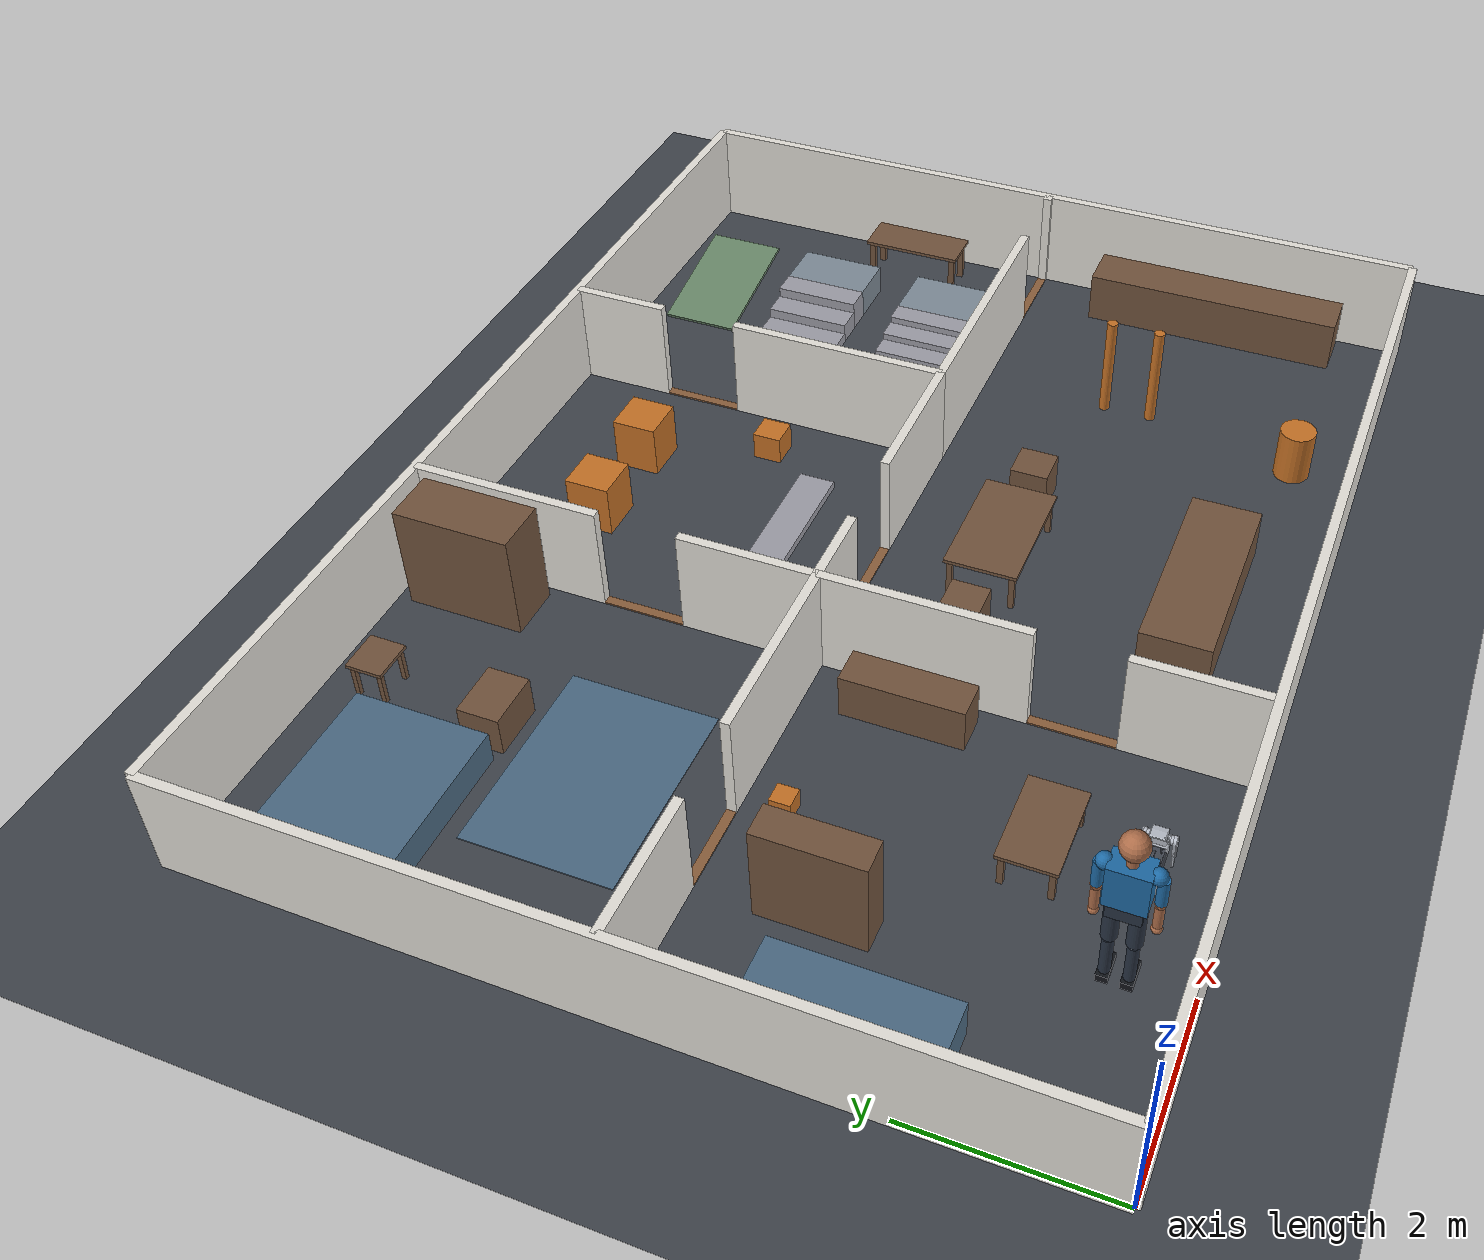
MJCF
<?xml version="1.0" ?>
<mujoco model="robodog_house">
  <compiler angle="radian" meshdir="/home/farouk/code/robodog/ros2_ws/install/robodog_description/share/robodog_description/meshes" autolimits="true" balanceinertia="true" discardvisual="false"/>
  <option timestep="0.0005" integrator="implicitfast" cone="elliptic" impratio="10" gravity="0 0 -9.81"/>
  <size njmax="2000" nconmax="500"/>
  <statistic extent="6.0"/>
  <visual>
    <global offwidth="1920" offheight="1200" azimuth="140" elevation="-20"/>
    <map znear="0.008333333333333333" zfar="10.0"/>
    <quality shadowsize="2048" offsamples="4"/>
  </visual>
  <default>
    <default class="robot">
      <joint damping="0.05" frictionloss="0.12" armature="0.012"/>
      <motor ctrllimited="true" ctrlrange="-36 36"/>
      <default class="visual">
        <geom contype="0" conaffinity="0" group="2" density="0"/>
      </default>
      <default class="collision">
        <geom group="3" condim="4" friction="0.9 0.02 0.001" solref="0.004 1" solimp="0.95 0.99 0.001" density="0" rgba="0.8 0.2 0.2 0.35"/>
      </default>
      <default class="foot">
        <geom group="3" condim="6" friction="1.0 0.05 0.002" solref="0.006 1" solimp="0.95 0.99 0.001" density="0" priority="2" rgba="0.1 0.1 0.12 1"/>
      </default>
    </default>
  </default>
  <asset>
    <mesh name="4x9x4_bearing" file="4x9x4_bearing.stl"/>
    <mesh name="61804_2rs" file="61804_2rs.stl"/>
    <mesh name="acs758_200a_sensor" file="acs758_200a_sensor.stl"/>
    <mesh name="albright_sw80_48v" file="albright_sw80_48v.stl"/>
    <mesh name="angle_motor_connect" file="angle_motor_connect.stl"/>
    <mesh name="as150u_socket" file="as150u_socket.stl"/>
    <mesh name="battery_6s_10000mah_1" file="battery_6s_10000mah_1.stl"/>
    <mesh name="battery_6s_10000mah_2" file="battery_6s_10000mah_2.stl"/>
    <mesh name="belt" file="belt.stl"/>
    <mesh name="bmi088_imu" file="bmi088_imu.stl"/>
    <mesh name="body" file="body.stl"/>
    <mesh name="body_front" file="body_front.stl"/>
    <mesh name="body_panel" file="body_panel.stl"/>
    <mesh name="body_rear" file="body_rear.stl"/>
    <mesh name="e_stop_mushroom_nc" file="e_stop_mushroom_nc.stl"/>
    <mesh name="electronics_deck_front" file="electronics_deck_front.stl"/>
    <mesh name="electronics_deck_rear" file="electronics_deck_rear.stl"/>
    <mesh name="foot_ball" file="foot_ball.stl"/>
    <mesh name="handle" file="handle.stl"/>
    <mesh name="head" file="head.stl"/>
    <mesh name="head_cover" file="head_cover.stl"/>
    <mesh name="idler_bolt_m4x30" file="idler_bolt_m4x30.stl"/>
    <mesh name="idler_roller" file="idler_roller.stl"/>
    <mesh name="imu_sassa_support" file="imu_sassa_support.stl"/>
    <mesh name="inline_connect" file="inline_connect.stl"/>
    <mesh name="jetson_orin_nano_super_8gb" file="jetson_orin_nano_super_8gb.stl"/>
    <mesh name="knee_output_hub" file="knee_output_hub.stl"/>
    <mesh name="knee_rear_plate" file="knee_rear_plate.stl"/>
    <mesh name="littelfuse_mega_100a_holder" file="littelfuse_mega_100a_holder.stl"/>
    <mesh name="lower_leg" file="lower_leg.stl"/>
    <mesh name="lower_leg_cover" file="lower_leg_cover.stl"/>
    <mesh name="meanwell_rsd_60l_12" file="meanwell_rsd_60l_12.stl"/>
    <mesh name="motor_pulley" file="motor_pulley.stl"/>
    <mesh name="nuwa_hp60c" file="nuwa_hp60c.stl"/>
    <mesh name="robstride06" file="robstride06.stl"/>
    <mesh name="upperleg_cover" file="upperleg_cover.stl"/>
    <mesh name="upperleg_main" file="upperleg_main.stl"/>
    <texture name="sky" type="skybox" builtin="gradient" rgb1="0.35 0.45 0.60" rgb2="0.08 0.10 0.14" width="256" height="256"/>
    <texture name="grid" type="2d" builtin="checker" width="512" height="512" rgb1="0.28 0.30 0.33" rgb2="0.22 0.24 0.27"/>
    <material name="grid" texture="grid" texrepeat="12 12" texuniform="true" reflectance="0.05"/>
    <material name="shell" rgba="0.26 0.28 0.32 1"/>
    <material name="actuator" rgba="0.88 0.42 0.09 1"/>
    <material name="structure" rgba="0.72 0.74 0.78 1"/>
    <material name="foot" rgba="0.10 0.10 0.12 1"/>
    <material name="bearing" rgba="0.62 0.81 0.93 1"/>
    <material name="sensor" rgba="0.13 0.55 0.75 1"/>
  </asset>
  <worldbody>
    <body name="base_link" childclass="robot" pos="3 0.7 0.34" quat="1 0 0 0">
      <freejoint name="base_free"/>
      <inertial pos="-0.00558 0.001349 -0.004841" mass="9.955898" fullinertia="0.043451 0.178524 0.201573 0.000934 -0.000384 -0.000473"/>
      <geom type="mesh" mesh="acs758_200a_sensor" class="visual" pos="0 0 0" quat="0.707105 0 0 -0.707108" material="structure"/>
      <geom type="mesh" mesh="albright_sw80_48v" class="visual" pos="0 0 0" quat="0.707105 0 0 -0.707108" material="structure"/>
      <geom type="mesh" mesh="as150u_socket" class="visual" pos="0 0 0" quat="0.707105 0 0 -0.707108" material="structure"/>
      <geom type="mesh" mesh="battery_6s_10000mah_1" class="visual" pos="0 0 0" quat="0.707105 0 0 -0.707108" material="structure"/>
      <geom type="mesh" mesh="battery_6s_10000mah_2" class="visual" pos="0 0 0" quat="0.707105 0 0 -0.707108" material="structure"/>
      <geom type="mesh" mesh="bmi088_imu" class="visual" pos="0 0 0" quat="0.707105 0 0 -0.707108" material="structure"/>
      <geom type="mesh" mesh="body" class="visual" pos="0 0 0" quat="0.707105 0 0 -0.707108" material="shell"/>
      <geom type="mesh" mesh="body_front" class="visual" pos="0 0 0" quat="0.707105 0 0 -0.707108" material="structure"/>
      <geom type="mesh" mesh="body_panel" class="visual" pos="0.198 -1e-06 0" quat="0.499998 0.5 -0.500002 -0.5" material="shell"/>
      <geom type="mesh" mesh="body_panel" class="visual" pos="-0.198 1e-06 0" quat="0.499998 -0.5 0.500002 -0.5" material="shell"/>
      <geom type="mesh" mesh="body_rear" class="visual" pos="0 0 0" quat="0.707105 0 0 -0.707108" material="structure"/>
      <geom type="mesh" mesh="e_stop_mushroom_nc" class="visual" pos="0 0 0" quat="0.707105 0 0 -0.707108" material="structure"/>
      <geom type="mesh" mesh="electronics_deck_front" class="visual" pos="0 0 0" quat="0.707105 0 0 -0.707108" material="structure"/>
      <geom type="mesh" mesh="electronics_deck_rear" class="visual" pos="0 0 0" quat="0.707105 0 0 -0.707108" material="structure"/>
      <geom type="mesh" mesh="handle" class="visual" pos="-0 0 0" quat="0.707105 0 0 -0.707108" material="shell"/>
      <geom type="mesh" mesh="head" class="visual" pos="0 0 0" quat="0.707105 0 0 -0.707108" material="structure"/>
      <geom type="mesh" mesh="head_cover" class="visual" pos="0 0 0" quat="0.707105 0 0 -0.707108" material="structure"/>
      <geom type="mesh" mesh="imu_sassa_support" class="visual" pos="0 0 0" quat="0.707105 0 0 -0.707108" material="structure"/>
      <geom type="mesh" mesh="jetson_orin_nano_super_8gb" class="visual" pos="0 0 0" quat="0.707105 0 0 -0.707108" material="structure"/>
      <geom type="mesh" mesh="littelfuse_mega_100a_holder" class="visual" pos="0 0 0" quat="0.707105 0 0 -0.707108" material="structure"/>
      <geom type="mesh" mesh="meanwell_rsd_60l_12" class="visual" pos="0 0 0" quat="0.707105 0 0 -0.707108" material="structure"/>
      <geom type="mesh" mesh="nuwa_hp60c" class="visual" pos="0 0 0" quat="0.707105 0 0 -0.707108" material="structure"/>
      <geom type="mesh" mesh="robstride06" class="visual" pos="0.227 -0.060001 0" quat="2.70595e-06 -0.707105 0.707108 -2.70596e-06" material="structure"/>
      <geom type="mesh" mesh="robstride06" class="visual" pos="-0.227 -0.06 0" quat="0.707105 0 0 -0.707108" material="structure"/>
      <geom type="mesh" mesh="robstride06" class="visual" pos="-0.227 0.060001 0" quat="0.707105 0 0 -0.707108" material="structure"/>
      <geom type="mesh" mesh="robstride06" class="visual" pos="0.227 0.059999 0" quat="2.70595e-06 -0.707105 0.707108 -2.70596e-06" material="structure"/>
      <geom name="base_col0" type="box" class="collision" size="0.192 0.11 0.06" pos="0 0 0" quat="1 0 0 0"/>
      <geom name="base_col1" type="cylinder" class="collision" size="0.044 0.0245" pos="-0.2065 -0.06 0" quat="0.499999 0.499999 -0.500001 -0.500001"/>
      <geom name="base_col2" type="cylinder" class="collision" size="0.044 0.0245" pos="-0.2065 0.060001 0" quat="0.499999 0.499999 -0.500001 -0.500001"/>
      <geom name="base_col3" type="cylinder" class="collision" size="0.044 0.0245" pos="0.2065 0.059999 0" quat="0.500001 -0.499997 0.499999 -0.500003"/>
      <geom name="base_col4" type="cylinder" class="collision" size="0.044 0.0245" pos="0.2065 -0.060001 0" quat="0.500001 -0.499997 0.499999 -0.500003"/>
      <site name="imu_site" pos="0 0 0" size="0.01" rgba="0.1 0.6 0.8 0.6"/>
      <body name="camera_link" pos="0.297 0.002036 0.108013" quat="1 0 0 0">
        <inertial pos="-0.01528 0 0" mass="0.15" diaginertia="0.0001 2e-05 0.00011"/>
        <site name="camera_site" pos="0 0 0" size="0.008" rgba="0.1 0.6 0.8 0.8"/>
        <camera name="depth_camera" mode="fixed" pos="0 0 0" quat="0.5 0.5 -0.5 -0.5" fovy="49"/>
      </body>
      <body name="FL_hip" pos="0.231 0.06 0">
        <joint name="FL_haa_joint" type="hinge" axis="1 0 0" range="-0.8 0.8" armature="0.012" damping="0.05" frictionloss="0.12"/>
        <inertial pos="0.049351 -0.010325 2.7e-05" mass="0.908648" fullinertia="0.000844 0.00132 0.001049 2.1e-05 2e-06 0"/>
        <geom type="mesh" mesh="angle_motor_connect" class="visual" pos="0.06 -0.017001 1e-06" quat="0.500004 0.499992 -0.499998 0.500006" material="structure"/>
        <geom type="mesh" mesh="robstride06" class="visual" pos="0.06 0.011999 0" quat="2.55155e-06 0.104523 1.15343e-05 0.994522" material="structure"/>
        <geom name="FL_hip_col0" type="box" class="collision" size="0.055 0.0275 0.0375" pos="0.03 0.008 0" quat="1 0 0 0"/>
        <geom name="FL_hip_col1" type="cylinder" class="collision" size="0.044 0.0245" pos="0.06 -0.008501 1e-06" quat="-0.0739073 0.0739109 0.703242 0.703225"/>
        <body name="FL_thigh" pos="0.06 0.016 0">
          <joint name="FL_hfe_joint" type="hinge" axis="0 1 0" range="-1.4 2.4" armature="0.012" damping="0.05" frictionloss="0.12"/>
          <inertial pos="2.7e-05 0.048393 -0.0284" mass="1.29223" fullinertia="0.004974 0.004899 0.0015 -1e-06 2e-06 0.000736"/>
          <geom type="mesh" mesh="4x9x4_bearing" class="visual" pos="0 0.053499 -1e-06" quat="-0.499997 0.500003 -0.500007 -0.499994" material="structure"/>
          <geom type="mesh" mesh="61804_2rs" class="visual" pos="0 0.079249 -1e-06" quat="1.18268e-05 1 -1.49999e-06 -5.00018e-07" material="bearing"/>
          <geom type="mesh" mesh="belt" class="visual" pos="0 0.053499 -1e-06" quat="-0.499997 0.500003 -0.500007 -0.499994" material="structure"/>
          <geom type="mesh" mesh="idler_bolt_m4x30" class="visual" pos="0 0.053499 -1e-06" quat="-0.499997 0.500003 -0.500007 -0.499994" material="structure"/>
          <geom type="mesh" mesh="idler_roller" class="visual" pos="0 0.053499 -1e-06" quat="-0.499997 0.500003 -0.500007 -0.499994" material="structure"/>
          <geom type="mesh" mesh="inline_connect" class="visual" pos="0 0.022999 -0" quat="6.92862e-06 0.707105 -9.29489e-06 -0.707108" material="structure"/>
          <geom type="mesh" mesh="knee_output_hub" class="visual" pos="0 0.055999 -1e-06" quat="0.7071 -0.707114 1.41422e-06 -7.07093e-07" material="structure"/>
          <geom type="mesh" mesh="knee_rear_plate" class="visual" pos="0 0.022999 -0" quat="6.92862e-06 0.707105 -9.29489e-06 -0.707108" material="structure"/>
          <geom type="mesh" mesh="motor_pulley" class="visual" pos="0 0.055999 -1e-06" quat="0.7071 -0.707114 1.41422e-06 -7.07093e-07" material="structure"/>
          <geom type="mesh" mesh="robstride06" class="visual" pos="0 0.051999 -1e-06" quat="1.18268e-05 1 -1.49999e-06 -5.00018e-07" material="structure"/>
          <geom type="mesh" mesh="upperleg_cover" class="visual" pos="0 0.053499 -1e-06" quat="-0.499997 0.500003 -0.500007 -0.499994" material="structure"/>
          <geom type="mesh" mesh="upperleg_main" class="visual" pos="0 0.053499 -1e-06" quat="-0.499997 0.500003 -0.500007 -0.499994" material="structure"/>
          <geom name="FL_thigh_col0" type="capsule" class="collision" size="0.03" fromto="0 0.034 -0.02 0 0.034 -0.177"/>
          <geom name="FL_thigh_col1" type="cylinder" class="collision" size="0.044 0.0245" pos="0 0.031499 -0" quat="0.707098 -0.707115 1.41422e-06 -7.0709e-07"/>
          <body name="FL_calf" pos="0 0.068501 -0.192">
            <joint name="FL_kfe_joint" type="hinge" axis="0 1 0" range="-2.6 0" armature="0.048" damping="0.2" frictionloss="0.24"/>
            <inertial pos="0 3.3e-05 -0.08012" mass="0.202465" fullinertia="0.00114 0.001145 3.2e-05 -0 -8e-06 0"/>
            <geom type="mesh" mesh="61804_2rs" class="visual" pos="0 -0.009006 -1e-06" quat="3.88215e-06 0.707107 -9.78396e-06 -0.707107" material="bearing"/>
            <geom type="mesh" mesh="61804_2rs" class="visual" pos="0 0.008994 -1e-06" quat="0.707107 -6.4795e-06 0.707107 -7.18661e-06" material="bearing"/>
            <geom type="mesh" mesh="foot_ball" class="visual" pos="0 -6e-06 -1e-06" quat="0.500004 0.499996 0.499994 -0.500006" material="foot"/>
            <geom type="mesh" mesh="lower_leg" class="visual" pos="0 -6e-06 -1e-06" quat="0.500004 0.499996 0.499994 -0.500006" material="structure"/>
            <geom type="mesh" mesh="lower_leg_cover" class="visual" pos="0 -6e-06 -1e-06" quat="0.500004 0.499996 0.499994 -0.500006" material="structure"/>
            <geom name="FL_calf_col0" type="capsule" class="collision" size="0.017" fromto="0 0 -0.015 0 0 -0.165621"/>
            <geom name="FL_calf_col1" type="sphere" class="foot" size="0.02" pos="0 0 -0.195621"/>
            <site name="FL_foot_site" pos="0 0 -0.195621" size="0.0204" type="sphere" rgba="0 0 0 0"/>
          </body>
        </body>
      </body>
      <body name="FR_hip" pos="0.231 -0.06 0">
        <joint name="FR_haa_joint" type="hinge" axis="1 0 0" range="-0.8 0.8" armature="0.012" damping="0.05" frictionloss="0.12"/>
        <inertial pos="0.049351 0.010323 -2.5e-05" mass="0.908648" fullinertia="0.000844 0.00132 0.001049 -2.1e-05 -2e-06 0"/>
        <geom type="mesh" mesh="angle_motor_connect" class="visual" pos="0.06 0.016999 1e-06" quat="0.500012 -0.499992 0.499991 0.500006" material="structure"/>
        <geom type="mesh" mesh="robstride06" class="visual" pos="0.06 -0.012001 0" quat="0.104531 3.64323e-06 0.994522 1.51833e-05" material="structure"/>
        <geom name="FR_hip_col0" type="box" class="collision" size="0.055 0.0275 0.0375" pos="0.03 -0.008 0" quat="1 0 0 0"/>
        <geom name="FR_hip_col1" type="cylinder" class="collision" size="0.044 0.0245" pos="0.06 0.008499 1e-06" quat="-0.0739118 -0.0739169 -0.703244 0.703222"/>
        <body name="FR_thigh" pos="0.06 -0.016 0">
          <joint name="FR_hfe_joint" type="hinge" axis="0 1 0" range="-1.4 2.4" armature="0.012" damping="0.05" frictionloss="0.12"/>
          <inertial pos="-2.7e-05 -0.048395 -0.028401" mass="1.29223" fullinertia="0.004974 0.004899 0.0015 -1e-06 -2e-06 -0.000736"/>
          <geom type="mesh" mesh="4x9x4_bearing" class="visual" pos="-0 -0.053501 -1e-06" quat="0.499992 0.500009 0.500005 -0.499995" material="structure"/>
          <geom type="mesh" mesh="61804_2rs" class="visual" pos="-0 -0.079251 -2e-06" quat="5.00037e-07 2.32679e-06 1 1.58268e-05" material="bearing"/>
          <geom type="mesh" mesh="belt" class="visual" pos="-0 -0.053501 -1e-06" quat="0.499992 0.500009 0.500005 -0.499995" material="structure"/>
          <geom type="mesh" mesh="idler_bolt_m4x30" class="visual" pos="-0 -0.053501 -1e-06" quat="0.499992 0.500009 0.500005 -0.499995" material="structure"/>
          <geom type="mesh" mesh="idler_roller" class="visual" pos="-0 -0.053501 -1e-06" quat="0.499992 0.500009 0.500005 -0.499995" material="structure"/>
          <geom type="mesh" mesh="inline_connect" class="visual" pos="-0 -0.023001 -0" quat="0.707108 1.23636e-05 0.707105 9.53512e-06" material="structure"/>
          <geom type="mesh" mesh="knee_output_hub" class="visual" pos="-0 -0.056001 -1e-06" quat="1.29171e-06 -1.99886e-06 -0.707117 0.707097" material="structure"/>
          <geom type="mesh" mesh="knee_rear_plate" class="visual" pos="-0 -0.023001 -0" quat="0.707108 1.23636e-05 0.707105 9.53512e-06" material="structure"/>
          <geom type="mesh" mesh="motor_pulley" class="visual" pos="-0 -0.056001 -1e-06" quat="1.29171e-06 -1.99886e-06 -0.707117 0.707097" material="structure"/>
          <geom type="mesh" mesh="robstride06" class="visual" pos="-0 -0.052001 -1e-06" quat="5.00037e-07 2.32679e-06 1 1.58268e-05" material="structure"/>
          <geom type="mesh" mesh="upperleg_cover" class="visual" pos="-0 -0.053501 -1e-06" quat="0.499992 0.500009 0.500005 -0.499995" material="structure"/>
          <geom type="mesh" mesh="upperleg_main" class="visual" pos="-0 -0.053501 -1e-06" quat="0.499992 0.500009 0.500005 -0.499995" material="structure"/>
          <geom name="FR_thigh_col0" type="capsule" class="collision" size="0.03" fromto="0 -0.034 -0.02 0 -0.034 -0.177"/>
          <geom name="FR_thigh_col1" type="cylinder" class="collision" size="0.044 0.0245" pos="-0 -0.031501 -1e-06" quat="1.29171e-06 -1.99887e-06 -0.707118 0.707096"/>
          <body name="FR_calf" pos="0 -0.068501 -0.192">
            <joint name="FR_kfe_joint" type="hinge" axis="0 1 0" range="-2.6 0" armature="0.048" damping="0.2" frictionloss="0.24"/>
            <inertial pos="-0 -3.3e-05 -0.080121" mass="0.202465" fullinertia="0.00114 0.001145 3.2e-05 0 -0 -0"/>
            <geom type="mesh" mesh="61804_2rs" class="visual" pos="-0 0.009005 -2e-06" quat="0.707107 1.49648e-05 0.707107 4.35818e-06" material="bearing"/>
            <geom type="mesh" mesh="61804_2rs" class="visual" pos="-0 -0.008995 -2e-06" quat="1.23674e-05 -0.707107 -6.95553e-06 0.707107" material="bearing"/>
            <geom type="mesh" mesh="foot_ball" class="visual" pos="-0 5e-06 -2e-06" quat="0.50001 -0.49999 0.499996 0.500004" material="foot"/>
            <geom type="mesh" mesh="lower_leg" class="visual" pos="-0 5e-06 -2e-06" quat="0.50001 -0.49999 0.499996 0.500004" material="structure"/>
            <geom type="mesh" mesh="lower_leg_cover" class="visual" pos="-0 5e-06 -2e-06" quat="0.50001 -0.49999 0.499996 0.500004" material="structure"/>
            <geom name="FR_calf_col0" type="capsule" class="collision" size="0.017" fromto="0 0 -0.015 0 0 -0.165621"/>
            <geom name="FR_calf_col1" type="sphere" class="foot" size="0.02" pos="0 0 -0.195621"/>
            <site name="FR_foot_site" pos="0 0 -0.195621" size="0.0204" type="sphere" rgba="0 0 0 0"/>
          </body>
        </body>
      </body>
      <body name="RL_hip" pos="-0.231 0.06 0">
        <joint name="RL_haa_joint" type="hinge" axis="1 0 0" range="-0.8 0.8" armature="0.012" damping="0.05" frictionloss="0.12"/>
        <inertial pos="-0.049351 -0.010323 -2.6e-05" mass="0.908648" fullinertia="0.000844 0.00132 0.001049 -2.1e-05 2e-06 -0"/>
        <geom type="mesh" mesh="angle_motor_connect" class="visual" pos="-0.06 -0.016999 0" quat="0.500001 0.499999 0.499997 -0.500003" material="structure"/>
        <geom type="mesh" mesh="robstride06" class="visual" pos="-0.06 0.012001 0" quat="1.55547e-06 0.994522 -2.29536e-06 -0.104527" material="structure"/>
        <geom name="RL_hip_col0" type="box" class="collision" size="0.055 0.0275 0.0375" pos="-0.03 0.008 0" quat="1 0 0 0"/>
        <geom name="RL_hip_col1" type="cylinder" class="collision" size="0.044 0.0245" pos="-0.06 -0.008499 0" quat="0.703232 -0.703234 0.0739132 0.0739099"/>
        <body name="RL_thigh" pos="-0.06 0.016 0">
          <joint name="RL_hfe_joint" type="hinge" axis="0 1 0" range="-1.4 2.4" armature="0.012" damping="0.05" frictionloss="0.12"/>
          <inertial pos="2.7e-05 0.048396 -0.0284" mass="1.29223" fullinertia="0.004974 0.004899 0.0015 -1e-06 2e-06 0.000736"/>
          <geom type="mesh" mesh="4x9x4_bearing" class="visual" pos="0 0.053501 -0" quat="-0.500002 0.499997 -0.500003 -0.499998" material="structure"/>
          <geom type="mesh" mesh="61804_2rs" class="visual" pos="1e-06 0.079251 -0" quat="1.82679e-06 1 -2e-06 -5.00004e-07" material="bearing"/>
          <geom type="mesh" mesh="belt" class="visual" pos="0 0.053501 -0" quat="-0.500002 0.499997 -0.500003 -0.499998" material="structure"/>
          <geom type="mesh" mesh="idler_bolt_m4x30" class="visual" pos="0 0.053501 -0" quat="-0.500002 0.499997 -0.500003 -0.499998" material="structure"/>
          <geom type="mesh" mesh="idler_roller" class="visual" pos="0 0.053501 -0" quat="-0.500002 0.499997 -0.500003 -0.499998" material="structure"/>
          <geom type="mesh" mesh="inline_connect" class="visual" pos="0 0.023001 -0" quat="-1.40629e-07 0.707105 -2.93275e-06 -0.707109" material="structure"/>
          <geom type="mesh" mesh="knee_output_hub" class="visual" pos="0 0.056001 -0" quat="0.707107 -0.707107 1.76777e-06 -1.06066e-06" material="structure"/>
          <geom type="mesh" mesh="knee_rear_plate" class="visual" pos="0 0.023001 -0" quat="-1.40629e-07 0.707105 -2.93275e-06 -0.707109" material="structure"/>
          <geom type="mesh" mesh="motor_pulley" class="visual" pos="0 0.056001 -0" quat="0.707107 -0.707107 1.76777e-06 -1.06066e-06" material="structure"/>
          <geom type="mesh" mesh="robstride06" class="visual" pos="0 0.052001 -0" quat="1.82679e-06 1 -2e-06 -5.00004e-07" material="structure"/>
          <geom type="mesh" mesh="upperleg_cover" class="visual" pos="0 0.053501 0" quat="-0.500002 0.499997 -0.500003 -0.499998" material="structure"/>
          <geom type="mesh" mesh="upperleg_main" class="visual" pos="0 0.053501 -0" quat="-0.500002 0.499997 -0.500003 -0.499998" material="structure"/>
          <geom name="RL_thigh_col0" type="capsule" class="collision" size="0.03" fromto="0 0.034 -0.02 0 0.034 -0.177"/>
          <geom name="RL_thigh_col1" type="cylinder" class="collision" size="0.044 0.0245" pos="0 0.031501 -0" quat="0.707105 -0.707108 1.76777e-06 -1.06066e-06"/>
          <body name="RL_calf" pos="0 0.068501 -0.192">
            <joint name="RL_kfe_joint" type="hinge" axis="0 1 0" range="-2.6 0" armature="0.048" damping="0.2" frictionloss="0.24"/>
            <inertial pos="0 4e-05 -0.080119" mass="0.202465" fullinertia="0.00114 0.001145 3.2e-05 -0 -7e-06 0"/>
            <geom type="mesh" mesh="61804_2rs" class="visual" pos="0 -0.009 -0" quat="3.05951e-06 -0.707107 3.05951e-06 0.707107" material="bearing"/>
            <geom type="mesh" mesh="61804_2rs" class="visual" pos="0 0.009 -0" quat="0.707107 7.07107e-07 0.707107 -7.07107e-07" material="bearing"/>
            <geom type="mesh" mesh="foot_ball" class="visual" pos="0 0 -0" quat="0.499999 0.500001 0.499998 -0.500001" material="foot"/>
            <geom type="mesh" mesh="lower_leg" class="visual" pos="0 0 -0" quat="0.499999 0.500001 0.499998 -0.500001" material="structure"/>
            <geom type="mesh" mesh="lower_leg_cover" class="visual" pos="0 0 -0" quat="0.499999 0.500001 0.499998 -0.500001" material="structure"/>
            <geom name="RL_calf_col0" type="capsule" class="collision" size="0.017" fromto="0 0 -0.015 0 0 -0.165621"/>
            <geom name="RL_calf_col1" type="sphere" class="foot" size="0.02" pos="0 0 -0.195621"/>
            <site name="RL_foot_site" pos="0 0 -0.195621" size="0.0204" type="sphere" rgba="0 0 0 0"/>
          </body>
        </body>
      </body>
      <body name="RR_hip" pos="-0.231 -0.06 0">
        <joint name="RR_haa_joint" type="hinge" axis="1 0 0" range="-0.8 0.8" armature="0.012" damping="0.05" frictionloss="0.12"/>
        <inertial pos="-0.049351 0.010325 2.6e-05" mass="0.908648" fullinertia="0.000844 0.00132 0.001049 2.1e-05 -2e-06 -0"/>
        <geom type="mesh" mesh="angle_motor_connect" class="visual" pos="-0.06 0.017001 -0" quat="-0.499997 0.500003 0.500001 0.499999" material="structure"/>
        <geom type="mesh" mesh="robstride06" class="visual" pos="-0.06 -0.011999 0" quat="0.994522 -2.09357e-06 -0.104527 -1.20358e-06" material="structure"/>
        <geom name="RR_hip_col0" type="box" class="collision" size="0.055 0.0275 0.0375" pos="-0.03 -0.008 0" quat="1 0 0 0"/>
        <geom name="RR_hip_col1" type="cylinder" class="collision" size="0.044 0.0245" pos="-0.06 0.008501 -0" quat="0.703235 0.703232 -0.0739124 0.0739107"/>
        <body name="RR_thigh" pos="-0.06 -0.016 0">
          <joint name="RR_hfe_joint" type="hinge" axis="0 1 0" range="-1.4 2.4" armature="0.012" damping="0.05" frictionloss="0.12"/>
          <inertial pos="-2.7e-05 -0.048394 -0.028399" mass="1.29223" fullinertia="0.004974 0.004899 0.0015 -1e-06 -2e-06 -0.000736"/>
          <geom type="mesh" mesh="4x9x4_bearing" class="visual" pos="-0 -0.053499 0" quat="0.500001 0.5 0.499996 -0.500004" material="structure"/>
          <geom type="mesh" mesh="61804_2rs" class="visual" pos="-0 -0.079249 0" quat="-4.99997e-07 -1.3268e-06 -1 2.3268e-06" material="bearing"/>
          <geom type="mesh" mesh="belt" class="visual" pos="-0 -0.053499 0" quat="0.500001 0.5 0.499996 -0.500004" material="structure"/>
          <geom type="mesh" mesh="idler_bolt_m4x30" class="visual" pos="-0 -0.053499 0" quat="0.500001 0.5 0.499996 -0.500004" material="structure"/>
          <geom type="mesh" mesh="idler_roller" class="visual" pos="-0 -0.053499 0" quat="0.500001 0.5 0.499996 -0.500004" material="structure"/>
          <geom type="mesh" mesh="inline_connect" class="visual" pos="-0 -0.022999 0" quat="0.707108 -5.41898e-07 0.707105 -2.66322e-06" material="structure"/>
          <geom type="mesh" mesh="knee_output_hub" class="visual" pos="-0 -0.055999 0" quat="5.84638e-07 -1.29174e-06 -0.707104 0.70711" material="structure"/>
          <geom type="mesh" mesh="knee_rear_plate" class="visual" pos="-0 -0.022999 0" quat="0.707108 -5.41898e-07 0.707105 -2.66322e-06" material="structure"/>
          <geom type="mesh" mesh="motor_pulley" class="visual" pos="-0 -0.055999 0" quat="5.84638e-07 -1.29174e-06 -0.707104 0.70711" material="structure"/>
          <geom type="mesh" mesh="robstride06" class="visual" pos="-0 -0.051999 0" quat="-4.99997e-07 -1.3268e-06 -1 2.3268e-06" material="structure"/>
          <geom type="mesh" mesh="upperleg_cover" class="visual" pos="-0 -0.053499 1e-06" quat="0.500001 0.5 0.499996 -0.500004" material="structure"/>
          <geom type="mesh" mesh="upperleg_main" class="visual" pos="-0 -0.053499 0" quat="0.500001 0.5 0.499996 -0.500004" material="structure"/>
          <geom name="RR_thigh_col0" type="capsule" class="collision" size="0.03" fromto="0 -0.034 -0.02 0 -0.034 -0.177"/>
          <geom name="RR_thigh_col1" type="cylinder" class="collision" size="0.044 0.0245" pos="-0 -0.031499 0" quat="5.84635e-07 -1.29174e-06 -0.707105 0.707108"/>
          <body name="RR_calf" pos="0 -0.068501 -0.192">
            <joint name="RR_kfe_joint" type="hinge" axis="0 1 0" range="-2.6 0" armature="0.048" damping="0.2" frictionloss="0.24"/>
            <inertial pos="-0 -4.1e-05 -0.080119" mass="0.202465" fullinertia="0.00114 0.001145 3.2e-05 0 -9e-06 -0"/>
            <geom type="mesh" mesh="61804_2rs" class="visual" pos="-0 0.009 0" quat="0.707107 2.00578e-06 0.707107 -7.18661e-06" material="bearing"/>
            <geom type="mesh" mesh="61804_2rs" class="visual" pos="-0 -0.009 0" quat="7.00172e-07 0.707107 -4.48065e-06 -0.707107" material="bearing"/>
            <geom type="mesh" mesh="foot_ball" class="visual" pos="-0 0 0" quat="0.500001 -0.5 0.500004 0.499996" material="foot"/>
            <geom type="mesh" mesh="lower_leg" class="visual" pos="-0 0 0" quat="0.500001 -0.5 0.500004 0.499996" material="structure"/>
            <geom type="mesh" mesh="lower_leg_cover" class="visual" pos="-0 0 0" quat="0.500001 -0.5 0.500004 0.499996" material="structure"/>
            <geom name="RR_calf_col0" type="capsule" class="collision" size="0.017" fromto="0 0 -0.015 0 0 -0.165621"/>
            <geom name="RR_calf_col1" type="sphere" class="foot" size="0.02" pos="0 0 -0.195621"/>
            <site name="RR_foot_site" pos="0 0 -0.195621" size="0.0204" type="sphere" rgba="0 0 0 0"/>
          </body>
        </body>
      </body>
    </body>
    <light name="sun" directional="true" diffuse="0.75 0.75 0.75" specular="0.1 0.1 0.1" pos="0 0 6" dir="0 0 -1" castshadow="true"/>
    <light name="fill" directional="true" diffuse="0.25 0.25 0.28" pos="-4 -4 5" dir="0.5 0.5 -1" castshadow="false"/>
    <geom name="ground" type="plane" material="grid" size="12 12 0.05" pos="6 4.5 0" condim="3" friction="0.9 0.02 0.001" group="0"/>
    <geom type="box" size="0.105 0.16 0.09" name="human190_pelvis" rgba="0.16 0.2 0.26 1" group="0" friction="0.9 0.02 0.001" condim="3" solref="0.004 1" solimp="0.95 0.99 0.001" pos="1.95 0.7 1.01" quat="1 0 0 0"/>
    <geom type="box" size="0.125 0.195 0.23" name="human190_torso" rgba="0.12 0.42 0.65 1" group="0" friction="0.9 0.02 0.001" condim="3" solref="0.004 1" solimp="0.95 0.99 0.001" pos="1.95 0.7 1.31" quat="1 0 0 0"/>
    <geom type="cylinder" size="0.055 0.045" name="human190_neck" rgba="0.68 0.43 0.29 1" group="0" friction="0.9 0.02 0.001" condim="3" solref="0.004 1" solimp="0.95 0.99 0.001" pos="1.95 0.7 1.585" quat="1 0 0 0"/>
    <geom type="sphere" size="0.135" name="human190_head" rgba="0.68 0.43 0.29 1" group="0" friction="0.9 0.02 0.001" condim="3" solref="0.004 1" solimp="0.95 0.99 0.001" pos="1.95 0.7 1.765" quat="1 0 0 0"/>
    <geom type="sphere" size="0.024" name="human190_nose" rgba="0.68 0.43 0.29 1" group="0" friction="0.9 0.02 0.001" condim="3" solref="0.004 1" solimp="0.95 0.99 0.001" pos="2.083 0.7 1.755" quat="1 0 0 0"/>
    <geom type="box" size="0.14 0.0575 0.04" name="human190_leftshoe" rgba="0.07 0.08 0.1 1" group="0" friction="0.9 0.02 0.001" condim="3" solref="0.004 1" solimp="0.95 0.99 0.001" pos="2.005 0.81 0.04" quat="1 0 0 0"/>
    <geom type="cylinder" size="0.055 0.22" name="human190_leftshin" rgba="0.16 0.2 0.26 1" group="0" friction="0.9 0.02 0.001" condim="3" solref="0.004 1" solimp="0.95 0.99 0.001" pos="1.95 0.81 0.3" quat="1 0 0 0"/>
    <geom type="sphere" size="0.06" name="human190_leftknee" rgba="0.16 0.2 0.26 1" group="0" friction="0.9 0.02 0.001" condim="3" solref="0.004 1" solimp="0.95 0.99 0.001" pos="1.95 0.81 0.55" quat="1 0 0 0"/>
    <geom type="cylinder" size="0.075 0.21" name="human190_leftthigh" rgba="0.16 0.2 0.26 1" group="0" friction="0.9 0.02 0.001" condim="3" solref="0.004 1" solimp="0.95 0.99 0.001" pos="1.95 0.81 0.77" quat="1 0 0 0"/>
    <geom type="sphere" size="0.08" name="human190_leftshoulder" rgba="0.12 0.42 0.65 1" group="0" friction="0.9 0.02 0.001" condim="3" solref="0.004 1" solimp="0.95 0.99 0.001" pos="1.95 0.925 1.485" quat="1 0 0 0"/>
    <geom type="cylinder" size="0.052 0.145" name="human190_leftupperarm" rgba="0.12 0.42 0.65 1" group="0" friction="0.9 0.02 0.001" condim="3" solref="0.004 1" solimp="0.95 0.99 0.001" pos="1.95 0.97 1.32" quat="1 0 0 0"/>
    <geom type="sphere" size="0.052" name="human190_leftelbow" rgba="0.68 0.43 0.29 1" group="0" friction="0.9 0.02 0.001" condim="3" solref="0.004 1" solimp="0.95 0.99 0.001" pos="1.95 0.97 1.16" quat="1 0 0 0"/>
    <geom type="cylinder" size="0.044 0.125" name="human190_leftforearm" rgba="0.68 0.43 0.29 1" group="0" friction="0.9 0.02 0.001" condim="3" solref="0.004 1" solimp="0.95 0.99 0.001" pos="1.95 0.97 1.005" quat="1 0 0 0"/>
    <geom type="sphere" size="0.05" name="human190_lefthand" rgba="0.68 0.43 0.29 1" group="0" friction="0.9 0.02 0.001" condim="3" solref="0.004 1" solimp="0.95 0.99 0.001" pos="1.95 0.97 0.835" quat="1 0 0 0"/>
    <geom type="sphere" size="0.009" name="human190_lefteye" rgba="0.07 0.08 0.1 1" group="0" friction="0.9 0.02 0.001" condim="3" solref="0.004 1" solimp="0.95 0.99 0.001" pos="2.072 0.745 1.8" quat="1 0 0 0"/>
    <geom type="box" size="0.14 0.0575 0.04" name="human190_rightshoe" rgba="0.07 0.08 0.1 1" group="0" friction="0.9 0.02 0.001" condim="3" solref="0.004 1" solimp="0.95 0.99 0.001" pos="2.005 0.59 0.04" quat="1 0 0 0"/>
    <geom type="cylinder" size="0.055 0.22" name="human190_rightshin" rgba="0.16 0.2 0.26 1" group="0" friction="0.9 0.02 0.001" condim="3" solref="0.004 1" solimp="0.95 0.99 0.001" pos="1.95 0.59 0.3" quat="1 0 0 0"/>
    <geom type="sphere" size="0.06" name="human190_rightknee" rgba="0.16 0.2 0.26 1" group="0" friction="0.9 0.02 0.001" condim="3" solref="0.004 1" solimp="0.95 0.99 0.001" pos="1.95 0.59 0.55" quat="1 0 0 0"/>
    <geom type="cylinder" size="0.075 0.21" name="human190_rightthigh" rgba="0.16 0.2 0.26 1" group="0" friction="0.9 0.02 0.001" condim="3" solref="0.004 1" solimp="0.95 0.99 0.001" pos="1.95 0.59 0.77" quat="1 0 0 0"/>
    <geom type="sphere" size="0.08" name="human190_rightshoulder" rgba="0.12 0.42 0.65 1" group="0" friction="0.9 0.02 0.001" condim="3" solref="0.004 1" solimp="0.95 0.99 0.001" pos="1.95 0.475 1.485" quat="1 0 0 0"/>
    <geom type="cylinder" size="0.052 0.145" name="human190_rightupperarm" rgba="0.12 0.42 0.65 1" group="0" friction="0.9 0.02 0.001" condim="3" solref="0.004 1" solimp="0.95 0.99 0.001" pos="1.95 0.43 1.32" quat="1 0 0 0"/>
    <geom type="sphere" size="0.052" name="human190_rightelbow" rgba="0.68 0.43 0.29 1" group="0" friction="0.9 0.02 0.001" condim="3" solref="0.004 1" solimp="0.95 0.99 0.001" pos="1.95 0.43 1.16" quat="1 0 0 0"/>
    <geom type="cylinder" size="0.044 0.125" name="human190_rightforearm" rgba="0.68 0.43 0.29 1" group="0" friction="0.9 0.02 0.001" condim="3" solref="0.004 1" solimp="0.95 0.99 0.001" pos="1.95 0.43 1.005" quat="1 0 0 0"/>
    <geom type="sphere" size="0.05" name="human190_righthand" rgba="0.68 0.43 0.29 1" group="0" friction="0.9 0.02 0.001" condim="3" solref="0.004 1" solimp="0.95 0.99 0.001" pos="1.95 0.43 0.835" quat="1 0 0 0"/>
    <geom type="sphere" size="0.009" name="human190_righteye" rgba="0.07 0.08 0.1 1" group="0" friction="0.9 0.02 0.001" condim="3" solref="0.004 1" solimp="0.95 0.99 0.001" pos="2.072 0.655 1.8" quat="1 0 0 0"/>
    <geom type="box" size="6 0.05 0.6" name="out_s_s0" rgba="0.9 0.89 0.86 1" group="0" friction="0.9 0.02 0.001" condim="3" solref="0.004 1" solimp="0.95 0.99 0.001" pos="6 0 0.6" quat="1 0 0 0"/>
    <geom type="box" size="4.5 0.05 0.6" name="out_e_s0" rgba="0.9 0.89 0.86 1" group="0" friction="0.9 0.02 0.001" condim="3" solref="0.004 1" solimp="0.95 0.99 0.001" pos="12 4.5 0.6" quat="0.707107 0 0 0.707107"/>
    <geom type="box" size="6 0.05 0.6" name="out_n_s0" rgba="0.9 0.89 0.86 1" group="0" friction="0.9 0.02 0.001" condim="3" solref="0.004 1" solimp="0.95 0.99 0.001" pos="6 9 0.6" quat="6.12323e-17 0 0 1"/>
    <geom type="box" size="4.5 0.05 0.6" name="out_w_s0" rgba="0.9 0.89 0.86 1" group="0" friction="0.9 0.02 0.001" condim="3" solref="0.004 1" solimp="0.95 0.99 0.001" pos="0 4.5 0.6" quat="0.707107 0 0 -0.707107"/>
    <geom type="box" size="0.7 0.05 0.6" name="div_living_kitchen_s0" rgba="0.9 0.89 0.86 1" group="0" friction="0.9 0.02 0.001" condim="3" solref="0.004 1" solimp="0.95 0.99 0.001" pos="4.5 0.7 0.6" quat="0.707107 0 0 0.707107"/>
    <geom type="box" size="1.1 0.05 0.6" name="div_living_kitchen_s1" rgba="0.9 0.89 0.86 1" group="0" friction="0.9 0.02 0.001" condim="3" solref="0.004 1" solimp="0.95 0.99 0.001" pos="4.5 3.4 0.6" quat="0.707107 0 0 0.707107"/>
    <geom type="box" size="0.45 0.05 0.01" name="div_living_kitchen_sill0" rgba="0.55 0.38 0.24 1" group="0" friction="0.9 0.02 0.001" condim="3" solref="0.004 1" solimp="0.95 0.99 0.001" pos="4.5 1.85 0.01" quat="0.707107 0 0 0.707107"/>
    <geom type="box" size="0.75 0.05 0.6" name="div_living_bed_s0" rgba="0.9 0.89 0.86 1" group="0" friction="0.9 0.02 0.001" condim="3" solref="0.004 1" solimp="0.95 0.99 0.001" pos="0.75 4.5 0.6" quat="1 0 0 0"/>
    <geom type="box" size="1.05 0.05 0.6" name="div_living_bed_s1" rgba="0.9 0.89 0.86 1" group="0" friction="0.9 0.02 0.001" condim="3" solref="0.004 1" solimp="0.95 0.99 0.001" pos="3.45 4.5 0.6" quat="1 0 0 0"/>
    <geom type="box" size="0.45 0.05 0.01" name="div_living_bed_sill0" rgba="0.55 0.38 0.24 1" group="0" friction="0.9 0.02 0.001" condim="3" solref="0.004 1" solimp="0.95 0.99 0.001" pos="1.95 4.5 0.01" quat="1 0 0 0"/>
    <geom type="box" size="0.75 0.05 0.6" name="div_bed_hall_s0" rgba="0.9 0.89 0.86 1" group="0" friction="0.9 0.02 0.001" condim="3" solref="0.004 1" solimp="0.95 0.99 0.001" pos="4.5 5.25 0.6" quat="0.707107 0 0 0.707107"/>
    <geom type="box" size="1.05 0.05 0.6" name="div_bed_hall_s1" rgba="0.9 0.89 0.86 1" group="0" friction="0.9 0.02 0.001" condim="3" solref="0.004 1" solimp="0.95 0.99 0.001" pos="4.5 7.95 0.6" quat="0.707107 0 0 0.707107"/>
    <geom type="box" size="0.45 0.05 0.01" name="div_bed_hall_sill0" rgba="0.55 0.38 0.24 1" group="0" friction="0.9 0.02 0.001" condim="3" solref="0.004 1" solimp="0.95 0.99 0.001" pos="4.5 6.45 0.01" quat="0.707107 0 0 0.707107"/>
    <geom type="box" size="0.45 0.05 0.6" name="div_kitchen_hall_s0" rgba="0.9 0.89 0.86 1" group="0" friction="0.9 0.02 0.001" condim="3" solref="0.004 1" solimp="0.95 0.99 0.001" pos="4.95 4.5 0.6" quat="1 0 0 0"/>
    <geom type="box" size="0.85 0.05 0.6" name="div_kitchen_hall_s1" rgba="0.9 0.89 0.86 1" group="0" friction="0.9 0.02 0.001" condim="3" solref="0.004 1" solimp="0.95 0.99 0.001" pos="7.15 4.5 0.6" quat="1 0 0 0"/>
    <geom type="box" size="0.45 0.05 0.01" name="div_kitchen_hall_sill0" rgba="0.55 0.38 0.24 1" group="0" friction="0.9 0.02 0.001" condim="3" solref="0.004 1" solimp="0.95 0.99 0.001" pos="5.85 4.5 0.01" quat="1 0 0 0"/>
    <geom type="box" size="1.5 0.05 0.6" name="div_kitchen_shop_s0" rgba="0.9 0.89 0.86 1" group="0" friction="0.9 0.02 0.001" condim="3" solref="0.004 1" solimp="0.95 0.99 0.001" pos="9.5 4.5 0.6" quat="1 0 0 0"/>
    <geom type="box" size="0.05 0.05 0.6" name="div_kitchen_shop_s1" rgba="0.9 0.89 0.86 1" group="0" friction="0.9 0.02 0.001" condim="3" solref="0.004 1" solimp="0.95 0.99 0.001" pos="11.95 4.5 0.6" quat="1 0 0 0"/>
    <geom type="box" size="0.45 0.05 0.01" name="div_kitchen_shop_sill0" rgba="0.55 0.38 0.24 1" group="0" friction="0.9 0.02 0.001" condim="3" solref="0.004 1" solimp="0.95 0.99 0.001" pos="11.45 4.5 0.01" quat="1 0 0 0"/>
    <geom type="box" size="1.25 0.05 0.6" name="div_hall_shop_s0" rgba="0.9 0.89 0.86 1" group="0" friction="0.9 0.02 0.001" condim="3" solref="0.004 1" solimp="0.95 0.99 0.001" pos="8 5.75 0.6" quat="0.707107 0 0 0.707107"/>
    <geom type="box" size="0.55 0.05 0.6" name="div_hall_shop_s1" rgba="0.9 0.89 0.86 1" group="0" friction="0.9 0.02 0.001" condim="3" solref="0.004 1" solimp="0.95 0.99 0.001" pos="8 8.45 0.6" quat="0.707107 0 0 0.707107"/>
    <geom type="box" size="0.45 0.05 0.01" name="div_hall_shop_sill0" rgba="0.55 0.38 0.24 1" group="0" friction="0.9 0.02 0.001" condim="3" solref="0.004 1" solimp="0.95 0.99 0.001" pos="8 7.45 0.01" quat="0.707107 0 0 0.707107"/>
    <geom type="box" size="0.425 0.9 0.22" name="sofa" rgba="0.3 0.42 0.52 1" group="0" friction="0.7 0.02 0.001" condim="3" solref="0.004 1" solimp="0.95 0.99 0.001" pos="0.55 2.6 0.22" quat="1 0 0 0"/>
    <geom type="box" size="0.175 0.55 0.55" name="bookshelf" rgba="0.45 0.33 0.24 1" group="0" friction="0.9 0.02 0.001" condim="3" solref="0.004 1" solimp="0.95 0.99 0.001" pos="1.6 3.3 0.55" quat="1 0 0 0"/>
    <geom type="box" size="0.5 0.3 0.02" name="coffee_table_top" rgba="0.45 0.33 0.24 1" group="0" friction="0.9 0.02 0.001" condim="3" solref="0.004 1" solimp="0.95 0.99 0.001" pos="3 1.7 0.38" quat="1 0 0 0"/>
    <geom type="box" size="0.03 0.03 0.18" name="coffee_table_leg0" rgba="0.45 0.33 0.24 1" group="0" friction="0.9 0.02 0.001" condim="3" solref="0.004 1" solimp="0.95 0.99 0.001" pos="3.44 1.94 0.18" quat="1 0 0 0"/>
    <geom type="box" size="0.03 0.03 0.18" name="coffee_table_leg1" rgba="0.45 0.33 0.24 1" group="0" friction="0.9 0.02 0.001" condim="3" solref="0.004 1" solimp="0.95 0.99 0.001" pos="2.56 1.94 0.18" quat="1 0 0 0"/>
    <geom type="box" size="0.03 0.03 0.18" name="coffee_table_leg2" rgba="0.45 0.33 0.24 1" group="0" friction="0.9 0.02 0.001" condim="3" solref="0.004 1" solimp="0.95 0.99 0.001" pos="3.44 1.46 0.18" quat="1 0 0 0"/>
    <geom type="box" size="0.03 0.03 0.18" name="coffee_table_leg3" rgba="0.45 0.33 0.24 1" group="0" friction="0.9 0.02 0.001" condim="3" solref="0.004 1" solimp="0.95 0.99 0.001" pos="2.56 1.46 0.18" quat="1 0 0 0"/>
    <geom type="box" size="0.2 0.65 0.25" name="tv_unit" rgba="0.45 0.33 0.24 1" group="0" friction="0.9 0.02 0.001" condim="3" solref="0.004 1" solimp="0.95 0.99 0.001" pos="4.1 3.4 0.25" quat="1 0 0 0"/>
    <body name="crate_a" pos="2.1 3.9 0.14" quat="1 0 0 0">
      <freejoint name="crate_a_free"/>
      <inertial pos="0 0 0" mass="1.2" diaginertia="0.01568 0.01568 0.01568"/>
      <geom type="box" size="0.14 0.14 0.14" name="crate_a" rgba="0.78 0.45 0.15 1" group="0" friction="0.9 0.02 0.001" condim="3" solref="0.004 1" solimp="0.95 0.99 0.001" pos="0 0 0"/>
    </body>
    <body name="crate_b" pos="2.6 4.05 0.11" quat="1 0 0 0">
      <freejoint name="crate_b_free"/>
      <inertial pos="0 0 0" mass="0.8" diaginertia="0.00645333 0.00645333 0.00645333"/>
      <geom type="box" size="0.11 0.11 0.11" name="crate_b" rgba="0.78 0.45 0.15 1" group="0" friction="0.9 0.02 0.001" condim="3" solref="0.004 1" solimp="0.95 0.99 0.001" pos="0 0 0"/>
    </body>
    <geom type="box" size="1 0.725 0.18" name="bed" rgba="0.3 0.42 0.52 1" group="0" friction="0.7 0.02 0.001" condim="3" solref="0.004 1" solimp="0.95 0.99 0.001" pos="1.15 7.6 0.18" quat="1 0 0 0"/>
    <geom type="box" size="0.3 0.65 0.6" name="wardrobe" rgba="0.45 0.33 0.24 1" group="0" friction="0.9 0.02 0.001" condim="3" solref="0.004 1" solimp="0.95 0.99 0.001" pos="4.05 8.15 0.6" quat="1 0 0 0"/>
    <geom type="box" size="0.225 0.2 0.02" name="nightstand_top" rgba="0.45 0.33 0.24 1" group="0" friction="0.9 0.02 0.001" condim="3" solref="0.004 1" solimp="0.95 0.99 0.001" pos="2.6 8.4 0.4" quat="1 0 0 0"/>
    <geom type="box" size="0.025 0.025 0.19" name="nightstand_leg0" rgba="0.45 0.33 0.24 1" group="0" friction="0.9 0.02 0.001" condim="3" solref="0.004 1" solimp="0.95 0.99 0.001" pos="2.775 8.55 0.19" quat="1 0 0 0"/>
    <geom type="box" size="0.025 0.025 0.19" name="nightstand_leg1" rgba="0.45 0.33 0.24 1" group="0" friction="0.9 0.02 0.001" condim="3" solref="0.004 1" solimp="0.95 0.99 0.001" pos="2.425 8.55 0.19" quat="1 0 0 0"/>
    <geom type="box" size="0.025 0.025 0.19" name="nightstand_leg2" rgba="0.45 0.33 0.24 1" group="0" friction="0.9 0.02 0.001" condim="3" solref="0.004 1" solimp="0.95 0.99 0.001" pos="2.775 8.25 0.19" quat="1 0 0 0"/>
    <geom type="box" size="0.025 0.025 0.19" name="nightstand_leg3" rgba="0.45 0.33 0.24 1" group="0" friction="0.9 0.02 0.001" condim="3" solref="0.004 1" solimp="0.95 0.99 0.001" pos="2.425 8.25 0.19" quat="1 0 0 0"/>
    <geom type="box" size="1.1 0.8 0.006" name="rug" rgba="0.3 0.42 0.52 1" group="0" friction="0.6 0.02 0.001" condim="3" solref="0.004 1" solimp="0.95 0.99 0.001" pos="2.3 5.9 0.006" quat="1 0 0 0"/>
    <geom type="box" size="0.3 0.225 0.22" name="chest" rgba="0.45 0.33 0.24 1" group="0" friction="0.9 0.02 0.001" condim="3" solref="0.004 1" solimp="0.95 0.99 0.001" pos="2.55 7.05 0.22" quat="1 0 0 0"/>
    <geom type="box" size="1.1 0.375 0.28" name="counter_island" rgba="0.45 0.33 0.24 1" group="0" friction="0.9 0.02 0.001" condim="3" solref="0.004 1" solimp="0.95 0.99 0.001" pos="6.6 1.15 0.28" quat="1 0 0 0"/>
    <geom type="box" size="0.275 1.5 0.3" name="counter_run" rgba="0.45 0.33 0.24 1" group="0" friction="0.9 0.02 0.001" condim="3" solref="0.004 1" solimp="0.95 0.99 0.001" pos="11.6 2.2 0.3" quat="1 0 0 0"/>
    <geom type="box" size="0.7 0.4 0.02" name="dining_table_top" rgba="0.45 0.33 0.24 1" group="0" friction="0.9 0.02 0.001" condim="3" solref="0.004 1" solimp="0.95 0.99 0.001" pos="6.6 3.3 0.44" quat="1 0 0 0"/>
    <geom type="box" size="0.03 0.03 0.21" name="dining_table_leg0" rgba="0.45 0.33 0.24 1" group="0" friction="0.9 0.02 0.001" condim="3" solref="0.004 1" solimp="0.95 0.99 0.001" pos="7.24 3.64 0.21" quat="1 0 0 0"/>
    <geom type="box" size="0.03 0.03 0.21" name="dining_table_leg1" rgba="0.45 0.33 0.24 1" group="0" friction="0.9 0.02 0.001" condim="3" solref="0.004 1" solimp="0.95 0.99 0.001" pos="5.96 3.64 0.21" quat="1 0 0 0"/>
    <geom type="box" size="0.03 0.03 0.21" name="dining_table_leg2" rgba="0.45 0.33 0.24 1" group="0" friction="0.9 0.02 0.001" condim="3" solref="0.004 1" solimp="0.95 0.99 0.001" pos="7.24 2.96 0.21" quat="1 0 0 0"/>
    <geom type="box" size="0.03 0.03 0.21" name="dining_table_leg3" rgba="0.45 0.33 0.24 1" group="0" friction="0.9 0.02 0.001" condim="3" solref="0.004 1" solimp="0.95 0.99 0.001" pos="5.96 2.96 0.21" quat="1 0 0 0"/>
    <geom type="box" size="0.21 0.21 0.23" name="chair0" rgba="0.45 0.33 0.24 1" group="0" friction="0.9 0.02 0.001" condim="3" solref="0.004 1" solimp="0.95 0.99 0.001" pos="5.45 3.3 0.23" quat="1 0 0 0"/>
    <geom type="box" size="0.21 0.21 0.23" name="chair1" rgba="0.45 0.33 0.24 1" group="0" friction="0.9 0.02 0.001" condim="3" solref="0.004 1" solimp="0.95 0.99 0.001" pos="7.75 3.3 0.23" quat="1 0 0 0"/>
    <body name="bin" pos="9.2 0.7 0.3" quat="1 0 0 0">
      <freejoint name="bin_free"/>
      <inertial pos="0 0 0" mass="2.0" diaginertia="0.0866667 0.0866667 0.0533333"/>
      <geom type="cylinder" size="0.2 0.3" name="bin" rgba="0.78 0.45 0.15 1" group="0" friction="0.9 0.02 0.001" condim="3" solref="0.004 1" solimp="0.95 0.99 0.001" pos="0 0 0"/>
    </body>
    <geom type="cylinder" size="0.06 0.6" name="pole_a" rgba="0.78 0.45 0.15 1" group="0" friction="0.9 0.02 0.001" condim="3" solref="0.004 1" solimp="0.95 0.99 0.001" pos="9.6 2.45 0.6" quat="1 0 0 0"/>
    <geom type="cylinder" size="0.06 0.6" name="pole_b" rgba="0.78 0.45 0.15 1" group="0" friction="0.9 0.02 0.001" condim="3" solref="0.004 1" solimp="0.95 0.99 0.001" pos="9.6 3 0.6" quat="1 0 0 0"/>
    <geom type="box" size="0.8 0.2 0.045" name="hall_step" rgba="0.62 0.62 0.66 1" group="0" friction="0.9 0.02 0.001" condim="3" solref="0.004 1" solimp="0.95 0.99 0.001" pos="6.25 5.6 0.045" quat="1 0 0 0"/>
    <geom type="box" size="0.25 0.25 0.3" name="hall_block_w" rgba="0.78 0.45 0.15 1" group="0" friction="0.9 0.02 0.001" condim="3" solref="0.004 1" solimp="0.95 0.99 0.001" pos="5.7 7.6 0.3" quat="1 0 0 0"/>
    <geom type="box" size="0.25 0.25 0.3" name="hall_block_e" rgba="0.78 0.45 0.15 1" group="0" friction="0.9 0.02 0.001" condim="3" solref="0.004 1" solimp="0.95 0.99 0.001" pos="6.8 7.6 0.3" quat="1 0 0 0"/>
    <body name="hall_crate" pos="7.4 6.3 0.16" quat="1 0 0 0">
      <freejoint name="hall_crate_free"/>
      <inertial pos="0 0 0" mass="1.5" diaginertia="0.0256 0.0256 0.0256"/>
      <geom type="box" size="0.16 0.16 0.16" name="hall_crate" rgba="0.78 0.45 0.15 1" group="0" friction="0.9 0.02 0.001" condim="3" solref="0.004 1" solimp="0.95 0.99 0.001" pos="0 0 0"/>
    </body>
    <geom type="box" size="0.13 0.55 0.04" name="stairs_low_step0" rgba="0.62 0.62 0.66 1" group="0" friction="0.9 0.02 0.001" condim="3" solref="0.004 1" solimp="0.95 0.99 0.001" pos="9.33 5.3 0.04" quat="1 0 0 0"/>
    <geom type="box" size="0.13 0.55 0.08" name="stairs_low_step1" rgba="0.62 0.62 0.66 1" group="0" friction="0.9 0.02 0.001" condim="3" solref="0.004 1" solimp="0.95 0.99 0.001" pos="9.59 5.3 0.08" quat="1 0 0 0"/>
    <geom type="box" size="0.13 0.55 0.12" name="stairs_low_step2" rgba="0.62 0.62 0.66 1" group="0" friction="0.9 0.02 0.001" condim="3" solref="0.004 1" solimp="0.95 0.99 0.001" pos="9.85 5.3 0.12" quat="1 0 0 0"/>
    <geom type="box" size="0.13 0.55 0.16" name="stairs_low_step3" rgba="0.62 0.62 0.66 1" group="0" friction="0.9 0.02 0.001" condim="3" solref="0.004 1" solimp="0.95 0.99 0.001" pos="10.11 5.3 0.16" quat="1 0 0 0"/>
    <geom type="box" size="0.35 0.55 0.16" name="stairs_low_landing" rgba="0.5 0.55 0.6 1" group="0" friction="0.9 0.02 0.001" condim="3" solref="0.004 1" solimp="0.95 0.99 0.001" pos="10.59 5.3 0.16" quat="1 0 0 0"/>
    <geom type="box" size="0.15 0.5 0.06" name="stairs_steep_step0" rgba="0.62 0.62 0.66 1" group="0" friction="0.9 0.02 0.001" condim="3" solref="0.004 1" solimp="0.95 0.99 0.001" pos="9.55 6.85 0.06" quat="1 0 0 0"/>
    <geom type="box" size="0.15 0.5 0.12" name="stairs_steep_step1" rgba="0.62 0.62 0.66 1" group="0" friction="0.9 0.02 0.001" condim="3" solref="0.004 1" solimp="0.95 0.99 0.001" pos="9.85 6.85 0.12" quat="1 0 0 0"/>
    <geom type="box" size="0.15 0.5 0.18" name="stairs_steep_step2" rgba="0.62 0.62 0.66 1" group="0" friction="0.9 0.02 0.001" condim="3" solref="0.004 1" solimp="0.95 0.99 0.001" pos="10.15 6.85 0.18" quat="1 0 0 0"/>
    <geom type="box" size="0.3 0.5 0.18" name="stairs_steep_landing" rgba="0.5 0.55 0.6 1" group="0" friction="0.9 0.02 0.001" condim="3" solref="0.004 1" solimp="0.95 0.99 0.001" pos="10.6 6.85 0.18" quat="1 0 0 0"/>
    <geom type="box" size="0.75 0.45 0.02" name="ramp_12deg" rgba="0.4 0.52 0.4 1" group="0" friction="0.9 0.02 0.001" condim="3" solref="0.004 1" solimp="0.95 0.99 0.001" pos="10.15 8.2 0.155934" quat="0.994522 0 -0.104528 0"/>
    <geom type="box" size="0.25 0.6 0.02" name="workbench_top" rgba="0.45 0.33 0.24 1" group="0" friction="0.9 0.02 0.001" condim="3" solref="0.004 1" solimp="0.95 0.99 0.001" pos="11.45 6.05 0.48" quat="1 0 0 0"/>
    <geom type="box" size="0.035 0.035 0.23" name="workbench_leg0" rgba="0.45 0.33 0.24 1" group="0" friction="0.9 0.02 0.001" condim="3" solref="0.004 1" solimp="0.95 0.99 0.001" pos="11.63 6.58 0.23" quat="1 0 0 0"/>
    <geom type="box" size="0.035 0.035 0.23" name="workbench_leg1" rgba="0.45 0.33 0.24 1" group="0" friction="0.9 0.02 0.001" condim="3" solref="0.004 1" solimp="0.95 0.99 0.001" pos="11.27 6.58 0.23" quat="1 0 0 0"/>
    <geom type="box" size="0.035 0.035 0.23" name="workbench_leg2" rgba="0.45 0.33 0.24 1" group="0" friction="0.9 0.02 0.001" condim="3" solref="0.004 1" solimp="0.95 0.99 0.001" pos="11.63 5.52 0.23" quat="1 0 0 0"/>
    <geom type="box" size="0.035 0.035 0.23" name="workbench_leg3" rgba="0.45 0.33 0.24 1" group="0" friction="0.9 0.02 0.001" condim="3" solref="0.004 1" solimp="0.95 0.99 0.001" pos="11.27 5.52 0.23" quat="1 0 0 0"/>
    <geom type="box" size="0.11 0.11 0.025" name="debris0" rgba="0.78 0.45 0.15 1" group="0" friction="0.9 0.02 0.001" condim="3" solref="0.004 1" solimp="0.95 0.99 0.001" pos="8.5 6.1 0.025" quat="1 0 0 0"/>
    <geom type="box" size="0.11 0.11 0.045" name="debris1" rgba="0.78 0.45 0.15 1" group="0" friction="0.9 0.02 0.001" condim="3" solref="0.004 1" solimp="0.95 0.99 0.001" pos="8.82 6.24 0.045" quat="1 0 0 0"/>
    <geom type="box" size="0.11 0.11 0.02" name="debris2" rgba="0.78 0.45 0.15 1" group="0" friction="0.9 0.02 0.001" condim="3" solref="0.004 1" solimp="0.95 0.99 0.001" pos="8.66 6.48 0.02" quat="1 0 0 0"/>
    <geom type="box" size="0.11 0.11 0.035" name="debris3" rgba="0.78 0.45 0.15 1" group="0" friction="0.9 0.02 0.001" condim="3" solref="0.004 1" solimp="0.95 0.99 0.001" pos="8.98 6.54 0.035" quat="1 0 0 0"/>
    <geom type="box" size="0.11 0.11 0.055" name="debris4" rgba="0.78 0.45 0.15 1" group="0" friction="0.9 0.02 0.001" condim="3" solref="0.004 1" solimp="0.95 0.99 0.001" pos="8.3 6.4 0.055" quat="1 0 0 0"/>
    <geom type="box" size="0.11 0.11 0.03" name="debris5" rgba="0.78 0.45 0.15 1" group="0" friction="0.9 0.02 0.001" condim="3" solref="0.004 1" solimp="0.95 0.99 0.001" pos="9.12 6.18 0.03" quat="1 0 0 0"/>
  </worldbody>
  <contact>
    <exclude name="FL_thigh_base" body1="base_link" body2="FL_thigh"/>
    <exclude name="FR_thigh_base" body1="base_link" body2="FR_thigh"/>
    <exclude name="RL_thigh_base" body1="base_link" body2="RL_thigh"/>
    <exclude name="RR_thigh_base" body1="base_link" body2="RR_thigh"/>
  </contact>
  <actuator>
    <motor name="FL_haa_joint" joint="FL_haa_joint" gear="1" class="robot" ctrlrange="-36 36"/>
    <motor name="FL_hfe_joint" joint="FL_hfe_joint" gear="1" class="robot" ctrlrange="-36 36"/>
    <motor name="FL_kfe_joint" joint="FL_kfe_joint" gear="1" class="robot" ctrlrange="-68.4 68.4"/>
    <motor name="FR_haa_joint" joint="FR_haa_joint" gear="1" class="robot" ctrlrange="-36 36"/>
    <motor name="FR_hfe_joint" joint="FR_hfe_joint" gear="1" class="robot" ctrlrange="-36 36"/>
    <motor name="FR_kfe_joint" joint="FR_kfe_joint" gear="1" class="robot" ctrlrange="-68.4 68.4"/>
    <motor name="RL_haa_joint" joint="RL_haa_joint" gear="1" class="robot" ctrlrange="-36 36"/>
    <motor name="RL_hfe_joint" joint="RL_hfe_joint" gear="1" class="robot" ctrlrange="-36 36"/>
    <motor name="RL_kfe_joint" joint="RL_kfe_joint" gear="1" class="robot" ctrlrange="-68.4 68.4"/>
    <motor name="RR_haa_joint" joint="RR_haa_joint" gear="1" class="robot" ctrlrange="-36 36"/>
    <motor name="RR_hfe_joint" joint="RR_hfe_joint" gear="1" class="robot" ctrlrange="-36 36"/>
    <motor name="RR_kfe_joint" joint="RR_kfe_joint" gear="1" class="robot" ctrlrange="-68.4 68.4"/>
  </actuator>
  <sensor>
    <accelerometer name="imu_accel" site="imu_site"/>
    <gyro name="imu_gyro" site="imu_site"/>
    <framequat name="imu_quat" objtype="site" objname="imu_site"/>
    <touch name="FL_touch" site="FL_foot_site"/>
    <touch name="FR_touch" site="FR_foot_site"/>
    <touch name="RL_touch" site="RL_foot_site"/>
    <touch name="RR_touch" site="RR_foot_site"/>
    <jointpos name="FL_haa_pos" joint="FL_haa_joint"/>
    <jointvel name="FL_haa_vel" joint="FL_haa_joint"/>
    <jointpos name="FL_hfe_pos" joint="FL_hfe_joint"/>
    <jointvel name="FL_hfe_vel" joint="FL_hfe_joint"/>
    <jointpos name="FL_kfe_pos" joint="FL_kfe_joint"/>
    <jointvel name="FL_kfe_vel" joint="FL_kfe_joint"/>
    <jointpos name="FR_haa_pos" joint="FR_haa_joint"/>
    <jointvel name="FR_haa_vel" joint="FR_haa_joint"/>
    <jointpos name="FR_hfe_pos" joint="FR_hfe_joint"/>
    <jointvel name="FR_hfe_vel" joint="FR_hfe_joint"/>
    <jointpos name="FR_kfe_pos" joint="FR_kfe_joint"/>
    <jointvel name="FR_kfe_vel" joint="FR_kfe_joint"/>
    <jointpos name="RL_haa_pos" joint="RL_haa_joint"/>
    <jointvel name="RL_haa_vel" joint="RL_haa_joint"/>
    <jointpos name="RL_hfe_pos" joint="RL_hfe_joint"/>
    <jointvel name="RL_hfe_vel" joint="RL_hfe_joint"/>
    <jointpos name="RL_kfe_pos" joint="RL_kfe_joint"/>
    <jointvel name="RL_kfe_vel" joint="RL_kfe_joint"/>
    <jointpos name="RR_haa_pos" joint="RR_haa_joint"/>
    <jointvel name="RR_haa_vel" joint="RR_haa_joint"/>
    <jointpos name="RR_hfe_pos" joint="RR_hfe_joint"/>
    <jointvel name="RR_hfe_vel" joint="RR_hfe_joint"/>
    <jointpos name="RR_kfe_pos" joint="RR_kfe_joint"/>
    <jointvel name="RR_kfe_vel" joint="RR_kfe_joint"/>
  </sensor>
  <keyframe>
    <key name="zero" qpos="3 0.7 0.409621 1 0 0 0 0 0 0 0 0 0 0 0 0 0 0 0 2.1 3.9 0.14 1 0 0 0 2.6 4.05 0.11 1 0 0 0 9.2 0.7 0.3 1 0 0 0 7.4 6.3 0.16 1 0 0 0"/>
    <key name="stand" qpos="3 0.7 0.322 1 0 0 0 0 0.693417 -1.37155 0 0.693417 -1.37155 0 0.693417 -1.37155 0 0.693417 -1.37155 2.1 3.9 0.14 1 0 0 0 2.6 4.05 0.11 1 0 0 0 9.2 0.7 0.3 1 0 0 0 7.4 6.3 0.16 1 0 0 0"/>
    <key name="crouch" qpos="3 0.7 0.242 1 0 0 0 0 0.980868 -1.93463 0 0.980868 -1.93463 0 0.980868 -1.93463 0 0.980868 -1.93463 2.1 3.9 0.14 1 0 0 0 2.6 4.05 0.11 1 0 0 0 9.2 0.7 0.3 1 0 0 0 7.4 6.3 0.16 1 0 0 0"/>
    <key name="rest" qpos="3 0.7 0.162 1 0 0 0 0 1.2255 -2.40276 0 1.2255 -2.40276 0 1.2255 -2.40276 0 1.2255 -2.40276 2.1 3.9 0.14 1 0 0 0 2.6 4.05 0.11 1 0 0 0 9.2 0.7 0.3 1 0 0 0 7.4 6.3 0.16 1 0 0 0"/>
  </keyframe>
</mujoco>
